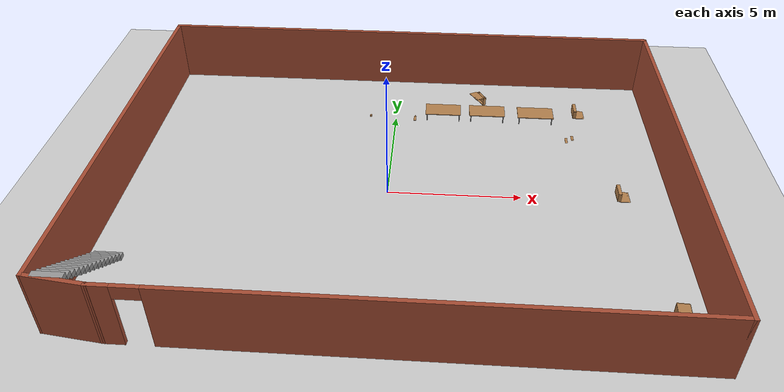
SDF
<sdf version="1.7">
 <world name="default">
  <plugin name="gazebo_link_attacher" filename="libgazebo_link_attacher.so"/>
  <light name="sun" type="directional">
   <pose>0 0 10 0 -0 0</pose>
   <diffuse>0.8 0.8 0.8 1</diffuse>
   <specular>0.2 0.2 0.2 1</specular>
   <attenuation>
    <range>1000</range>
    <constant>0.9</constant>
    <linear>0.01</linear>
    <quadratic>0.001</quadratic>
   </attenuation>
   <direction>-0.5 0.1 -0.9</direction>
   <spot><inner_angle>0</inner_angle><outer_angle>0</outer_angle><falloff>0</falloff></spot>
  </light>
  <model name="ground_plane">
   <static>1</static>
   <link name="link">
    <collision name="collision">
     <geometry><plane><normal>0 0 1</normal><size>100 100</size></plane></geometry>
     <surface><friction><ode><mu>100</mu><mu2>50</mu2></ode></friction></surface>
    </collision>
    <visual name="visual">
     <cast_shadows>0</cast_shadows>
     <geometry><plane><normal>0 0 1</normal><size>100 100</size></plane></geometry>
     <material>
      <script><uri>file://media/materials/scripts/gazebo.material</uri><name>Gazebo/Grey</name></script>
     </material>
    </visual>
   </link>
  </model>
  <gravity>0 0 -9.8</gravity>
  <magnetic_field>6e-06 2.3e-05 -4.2e-05</magnetic_field>
  <atmosphere type="adiabatic"/>
  <physics type="ode">
   <max_step_size>0.001</max_step_size>
   <real_time_factor>1</real_time_factor>
   <real_time_update_rate>1000</real_time_update_rate>
  </physics>
  <scene><ambient>0.4 0.4 0.4 1</ambient><background>0.7 0.7 0.7 1</background><shadows>1</shadows></scene>
  <audio><device>default</device></audio>
  <spherical_coordinates>
   <surface_model>EARTH_WGS84</surface_model>
   <latitude_deg>0</latitude_deg>
   <longitude_deg>0</longitude_deg>
   <elevation>0</elevation>
   <heading_deg>0</heading_deg>
  </spherical_coordinates>
  <model name="Untitled">
   <pose>0.302416 0.205559 0 0 -0 0</pose>
   <link name="Stairs_0">
    <visual name="Stairs_0_Visual_0">
     <pose>-9.52086 -4.35961 0.083333 0 -0 0</pose>
     <geometry><box><size>1 0.233333 0.166667</size></box></geometry>
     <material>
      <script><uri>file://media/materials/scripts/gazebo.material</uri><name>Gazebo/Grey</name></script>
      <ambient>1 1 1 1</ambient>
     </material>
     <meta><layer>0</layer></meta>
    </visual>
    <collision name="Stairs_0_Collision_0">
     <geometry><box><size>1 0.233333 0.166667</size></box></geometry>
     <pose>-9.52086 -4.35961 0.083333 0 -0 0</pose>
    </collision>
    <visual name="Stairs_0_Visual_1">
     <pose>-9.52086 -4.59294 0.25 0 -0 0</pose>
     <geometry><box><size>1 0.233333 0.166667</size></box></geometry>
     <material>
      <script><uri>file://media/materials/scripts/gazebo.material</uri><name>Gazebo/Grey</name></script>
      <ambient>1 1 1 1</ambient>
     </material>
     <meta><layer>0</layer></meta>
    </visual>
    <collision name="Stairs_0_Collision_1">
     <geometry><box><size>1 0.233333 0.166667</size></box></geometry>
     <pose>-9.52086 -4.59294 0.25 0 -0 0</pose>
    </collision>
    <visual name="Stairs_0_Visual_2">
     <pose>-9.52086 -4.82628 0.416667 0 -0 0</pose>
     <geometry><box><size>1 0.233333 0.166667</size></box></geometry>
     <material>
      <script><uri>file://media/materials/scripts/gazebo.material</uri><name>Gazebo/Grey</name></script>
      <ambient>1 1 1 1</ambient>
     </material>
     <meta><layer>0</layer></meta>
    </visual>
    <collision name="Stairs_0_Collision_2">
     <geometry><box><size>1 0.233333 0.166667</size></box></geometry>
     <pose>-9.52086 -4.82628 0.416667 0 -0 0</pose>
    </collision>
    <visual name="Stairs_0_Visual_3">
     <pose>-9.52086 -5.05961 0.583333 0 -0 0</pose>
     <geometry><box><size>1 0.233333 0.166667</size></box></geometry>
     <material>
      <script><uri>file://media/materials/scripts/gazebo.material</uri><name>Gazebo/Grey</name></script>
      <ambient>1 1 1 1</ambient>
     </material>
     <meta><layer>0</layer></meta>
    </visual>
    <collision name="Stairs_0_Collision_3">
     <geometry><box><size>1 0.233333 0.166667</size></box></geometry>
     <pose>-9.52086 -5.05961 0.583333 0 -0 0</pose>
    </collision>
    <visual name="Stairs_0_Visual_4">
     <pose>-9.52086 -5.29294 0.75 0 -0 0</pose>
     <geometry><box><size>1 0.233333 0.166667</size></box></geometry>
     <material>
      <script><uri>file://media/materials/scripts/gazebo.material</uri><name>Gazebo/Grey</name></script>
      <ambient>1 1 1 1</ambient>
     </material>
     <meta><layer>0</layer></meta>
    </visual>
    <collision name="Stairs_0_Collision_4">
     <geometry><box><size>1 0.233333 0.166667</size></box></geometry>
     <pose>-9.52086 -5.29294 0.75 0 -0 0</pose>
    </collision>
    <visual name="Stairs_0_Visual_5">
     <pose>-9.52086 -5.52628 0.916667 0 -0 0</pose>
     <geometry><box><size>1 0.233333 0.166667</size></box></geometry>
     <material>
      <script><uri>file://media/materials/scripts/gazebo.material</uri><name>Gazebo/Grey</name></script>
      <ambient>1 1 1 1</ambient>
     </material>
     <meta><layer>0</layer></meta>
    </visual>
    <collision name="Stairs_0_Collision_5">
     <geometry><box><size>1 0.233333 0.166667</size></box></geometry>
     <pose>-9.52086 -5.52628 0.916667 0 -0 0</pose>
    </collision>
    <visual name="Stairs_0_Visual_6">
     <pose>-9.52086 -5.75961 1.08333 0 -0 0</pose>
     <geometry><box><size>1 0.233333 0.166667</size></box></geometry>
     <material>
      <script><uri>file://media/materials/scripts/gazebo.material</uri><name>Gazebo/Grey</name></script>
      <ambient>1 1 1 1</ambient>
     </material>
     <meta><layer>0</layer></meta>
    </visual>
    <collision name="Stairs_0_Collision_6">
     <geometry><box><size>1 0.233333 0.166667</size></box></geometry>
     <pose>-9.52086 -5.75961 1.08333 0 -0 0</pose>
    </collision>
    <visual name="Stairs_0_Visual_7">
     <pose>-9.52086 -5.99294 1.25 0 -0 0</pose>
     <geometry><box><size>1 0.233333 0.166667</size></box></geometry>
     <material>
      <script><uri>file://media/materials/scripts/gazebo.material</uri><name>Gazebo/Grey</name></script>
      <ambient>1 1 1 1</ambient>
     </material>
     <meta><layer>0</layer></meta>
    </visual>
    <collision name="Stairs_0_Collision_7">
     <geometry><box><size>1 0.233333 0.166667</size></box></geometry>
     <pose>-9.52086 -5.99294 1.25 0 -0 0</pose>
    </collision>
    <visual name="Stairs_0_Visual_8">
     <pose>-9.52086 -6.22628 1.41667 0 -0 0</pose>
     <geometry><box><size>1 0.233333 0.166667</size></box></geometry>
     <material>
      <script><uri>file://media/materials/scripts/gazebo.material</uri><name>Gazebo/Grey</name></script>
      <ambient>1 1 1 1</ambient>
     </material>
     <meta><layer>0</layer></meta>
    </visual>
    <collision name="Stairs_0_Collision_8">
     <geometry><box><size>1 0.233333 0.166667</size></box></geometry>
     <pose>-9.52086 -6.22628 1.41667 0 -0 0</pose>
    </collision>
    <visual name="Stairs_0_Visual_9">
     <pose>-9.52086 -6.45961 1.58333 0 -0 0</pose>
     <geometry><box><size>1 0.233333 0.166667</size></box></geometry>
     <material>
      <script><uri>file://media/materials/scripts/gazebo.material</uri><name>Gazebo/Grey</name></script>
      <ambient>1 1 1 1</ambient>
     </material>
     <meta><layer>0</layer></meta>
    </visual>
    <collision name="Stairs_0_Collision_9">
     <geometry><box><size>1 0.233333 0.166667</size></box></geometry>
     <pose>-9.52086 -6.45961 1.58333 0 -0 0</pose>
    </collision>
    <visual name="Stairs_0_Visual_10">
     <pose>-9.52086 -6.69294 1.75 0 -0 0</pose>
     <geometry><box><size>1 0.233333 0.166667</size></box></geometry>
     <material>
      <script><uri>file://media/materials/scripts/gazebo.material</uri><name>Gazebo/Grey</name></script>
      <ambient>1 1 1 1</ambient>
     </material>
     <meta><layer>0</layer></meta>
    </visual>
    <collision name="Stairs_0_Collision_10">
     <geometry><box><size>1 0.233333 0.166667</size></box></geometry>
     <pose>-9.52086 -6.69294 1.75 0 -0 0</pose>
    </collision>
    <visual name="Stairs_0_Visual_11">
     <pose>-9.52086 -6.92628 1.91667 0 -0 0</pose>
     <geometry><box><size>1 0.233333 0.166667</size></box></geometry>
     <material>
      <script><uri>file://media/materials/scripts/gazebo.material</uri><name>Gazebo/Grey</name></script>
      <ambient>1 1 1 1</ambient>
     </material>
     <meta><layer>0</layer></meta>
    </visual>
    <collision name="Stairs_0_Collision_11">
     <geometry><box><size>1 0.233333 0.166667</size></box></geometry>
     <pose>-9.52086 -6.92628 1.91667 0 -0 0</pose>
    </collision>
    <visual name="Stairs_0_Visual_12">
     <pose>-9.52086 -7.15961 2.08333 0 -0 0</pose>
     <geometry><box><size>1 0.233333 0.166667</size></box></geometry>
     <material>
      <script><uri>file://media/materials/scripts/gazebo.material</uri><name>Gazebo/Grey</name></script>
      <ambient>1 1 1 1</ambient>
     </material>
     <meta><layer>0</layer></meta>
    </visual>
    <collision name="Stairs_0_Collision_12">
     <geometry><box><size>1 0.233333 0.166667</size></box></geometry>
     <pose>-9.52086 -7.15961 2.08333 0 -0 0</pose>
    </collision>
    <visual name="Stairs_0_Visual_13">
     <pose>-9.52086 -7.39294 2.25 0 -0 0</pose>
     <geometry><box><size>1 0.233333 0.166667</size></box></geometry>
     <material>
      <script><uri>file://media/materials/scripts/gazebo.material</uri><name>Gazebo/Grey</name></script>
      <ambient>1 1 1 1</ambient>
     </material>
     <meta><layer>0</layer></meta>
    </visual>
    <collision name="Stairs_0_Collision_13">
     <geometry><box><size>1 0.233333 0.166667</size></box></geometry>
     <pose>-9.52086 -7.39294 2.25 0 -0 0</pose>
    </collision>
    <visual name="Stairs_0_Visual_14">
     <pose>-9.52086 -7.62628 2.41667 0 -0 0</pose>
     <geometry><box><size>1 0.233333 0.166667</size></box></geometry>
     <material>
      <script><uri>file://media/materials/scripts/gazebo.material</uri><name>Gazebo/Grey</name></script>
      <ambient>1 1 1 1</ambient>
     </material>
     <meta><layer>0</layer></meta>
    </visual>
    <collision name="Stairs_0_Collision_14">
     <geometry><box><size>1 0.233333 0.166667</size></box></geometry>
     <pose>-9.52086 -7.62628 2.41667 0 -0 0</pose>
    </collision>
   </link>
   <link name="Wall_1">
    <pose>1.00436 -7.92064 0 0 -0 0</pose>
    <visual name="Wall_1_Visual_0">
     <pose>-8.99137 0 1.25 0 -0 0</pose>
     <geometry><box><size>0.767258 0.15 2.5</size></box></geometry>
     <material>
      <script><uri>file://media/materials/scripts/gazebo.material</uri><name>Gazebo/Bricks</name></script>
      <ambient>1 1 1 1</ambient>
     </material>
     <meta><layer>0</layer></meta>
    </visual>
    <collision name="Wall_1_Collision_0">
     <geometry><box><size>0.767258 0.15 2.5</size></box></geometry>
     <pose>-8.99137 0 1.25 0 -0 0</pose>
    </collision>
    <visual name="Wall_1_Visual_1">
     <pose>0.833629 0 1.25 0 -0 0</pose>
     <geometry><box><size>17.0827 0.15 2.5</size></box></geometry>
     <material>
      <script><uri>file://media/materials/scripts/gazebo.material</uri><name>Gazebo/Bricks</name></script>
      <ambient>1 1 1 1</ambient>
     </material>
     <meta><layer>0</layer></meta>
    </visual>
    <collision name="Wall_1_Collision_1">
     <geometry><box><size>17.0827 0.15 2.5</size></box></geometry>
     <pose>0.833629 0 1.25 0 -0 0</pose>
    </collision>
    <visual name="Wall_1_Visual_2">
     <pose>-8.15774 0 2.25 0 -0 0</pose>
     <geometry><box><size>0.9 0.15 0.5</size></box></geometry>
     <material>
      <script><uri>file://media/materials/scripts/gazebo.material</uri><name>Gazebo/Bricks</name></script>
      <ambient>1 1 1 1</ambient>
     </material>
     <meta><layer>0</layer></meta>
    </visual>
    <collision name="Wall_1_Collision_2">
     <geometry><box><size>0.9 0.15 0.5</size></box></geometry>
     <pose>-8.15774 0 2.25 0 -0 0</pose>
    </collision>
   </link>
   <link name="Wall_2">
    <collision name="Wall_2_Collision">
     <geometry><box><size>16 0.15 2.5</size></box></geometry>
     <pose>0 0 1.25 0 -0 0</pose>
    </collision>
    <visual name="Wall_2_Visual">
     <pose>0 0 1.25 0 -0 0</pose>
     <geometry><box><size>16 0.15 2.5</size></box></geometry>
     <material>
      <script><uri>file://media/materials/scripts/gazebo.material</uri><name>Gazebo/Bricks</name></script>
      <ambient>1 1 1 1</ambient>
     </material>
     <meta><layer>0</layer></meta>
    </visual>
    <pose>10.3044 0.004361 0 0 -0 1.5708</pose>
   </link>
   <link name="Wall_3">
    <collision name="Wall_3_Collision">
     <geometry><box><size>20.75 0.15 2.5</size></box></geometry>
     <pose>0 0 1.25 0 -0 0</pose>
    </collision>
    <visual name="Wall_3_Visual">
     <pose>0 0 1.25 0 -0 0</pose>
     <geometry><box><size>20.75 0.15 2.5</size></box></geometry>
     <material>
      <script><uri>file://media/materials/scripts/gazebo.material</uri><name>Gazebo/Bricks</name></script>
      <ambient>1 1 1 1</ambient>
     </material>
     <meta><layer>0</layer></meta>
    </visual>
    <pose>0.004362 7.92936 0 0 -0 3.14159</pose>
   </link>
   <link name="Wall_4">
    <collision name="Wall_4_Collision">
     <geometry><box><size>15.75 0.15 2.5</size></box></geometry>
     <pose>0 0 1.25 0 -0 0</pose>
    </collision>
    <visual name="Wall_4_Visual">
     <pose>0 0 1.25 0 -0 0</pose>
     <geometry><box><size>15.75 0.15 2.5</size></box></geometry>
     <material>
      <script><uri>file://media/materials/scripts/gazebo.material</uri><name>Gazebo/Bricks</name></script>
      <ambient>1 1 1 1</ambient>
     </material>
     <meta><layer>0</layer></meta>
    </visual>
    <pose>-10.2956 0.129361 0 0 -0 -1.5708</pose>
   </link>
   <link name="Wall_5">
    <collision name="Wall_5_Collision">
     <geometry><box><size>2.16556 0.15 2.5</size></box></geometry>
     <pose>0 0 1.25 0 -0 0</pose>
    </collision>
    <visual name="Wall_5_Visual">
     <pose>0 0 1.25 0 -0 0</pose>
     <geometry><box><size>2.16556 0.15 2.5</size></box></geometry>
     <material>
      <script><uri>file://media/materials/scripts/gazebo.material</uri><name>Gazebo/Bricks</name></script>
      <ambient>1 1 1 1</ambient>
     </material>
     <meta><layer>0</layer></meta>
    </visual>
    <pose>-9.29564 -7.79564 0 0 -0 -0.124355</pose>
   </link>
   <static>1</static>
  </model>
  <model name="table">
   <static>1</static>
   <link name="link">
    <collision name="surface">
     <pose>0 0 1 0 -0 0</pose>
     <geometry><box><size>1.5 0.8 0.03</size></box></geometry>
     <surface><friction><ode><mu>0.6</mu><mu2>0.6</mu2></ode></friction></surface>
    </collision>
    <visual name="visual1">
     <pose>0 0 1 0 -0 0</pose>
     <geometry><box><size>1.5 0.8 0.03</size></box></geometry>
     <material>
      <script><uri>file://media/materials/scripts/gazebo.material</uri><name>Gazebo/Wood</name></script>
     </material>
    </visual>
    <collision name="front_left_leg">
     <pose>0.68 0.38 0.5 0 -0 0</pose>
     <geometry><cylinder><radius>0.02</radius><length>1</length></cylinder></geometry>
    </collision>
    <visual name="front_left_leg">
     <pose>0.68 0.38 0.5 0 -0 0</pose>
     <geometry><cylinder><radius>0.02</radius><length>1</length></cylinder></geometry>
     <material>
      <script><uri>file://media/materials/scripts/gazebo.material</uri><name>Gazebo/Grey</name></script>
     </material>
    </visual>
    <collision name="front_right_leg">
     <pose>0.68 -0.38 0.5 0 -0 0</pose>
     <geometry><cylinder><radius>0.02</radius><length>1</length></cylinder></geometry>
    </collision>
    <visual name="front_right_leg">
     <pose>0.68 -0.38 0.5 0 -0 0</pose>
     <geometry><cylinder><radius>0.02</radius><length>1</length></cylinder></geometry>
     <material>
      <script><uri>file://media/materials/scripts/gazebo.material</uri><name>Gazebo/Grey</name></script>
     </material>
    </visual>
    <collision name="back_right_leg">
     <pose>-0.68 -0.38 0.5 0 -0 0</pose>
     <geometry><cylinder><radius>0.02</radius><length>1</length></cylinder></geometry>
    </collision>
    <visual name="back_right_leg">
     <pose>-0.68 -0.38 0.5 0 -0 0</pose>
     <geometry><cylinder><radius>0.02</radius><length>1</length></cylinder></geometry>
     <material>
      <script><uri>file://media/materials/scripts/gazebo.material</uri><name>Gazebo/Grey</name></script>
     </material>
    </visual>
    <collision name="back_left_leg">
     <pose>-0.68 0.38 0.5 0 -0 0</pose>
     <geometry><cylinder><radius>0.02</radius><length>1</length></cylinder></geometry>
    </collision>
    <visual name="back_left_leg">
     <pose>-0.68 0.38 0.5 0 -0 0</pose>
     <geometry><cylinder><radius>0.02</radius><length>1</length></cylinder></geometry>
     <material>
      <script><uri>file://media/materials/scripts/gazebo.material</uri><name>Gazebo/Grey</name></script>
     </material>
    </visual>
   </link>
   <pose>5.91005 5.39504 -0.713216 0 -0 0</pose>
  </model>
  <model name="wooden_board">
   <link name="base">
    <pose>0 0 0.00523 0 -0 0</pose>
    <inertial>
     <mass>0.2765</mass>
     <inertia>
      <ixx>0.0025148</ixx>
      <ixy>0</ixy>
      <ixz>0</ixz>
      <iyy>0.00024037</iyy>
      <iyz>0</iyz>
      <izz>0.00275013</izz>
     </inertia>
    </inertial>
    <collision name="collision">
     <geometry><box><size>0.1016 0.3302 0.01046</size></box></geometry>
     <surface>
      <contact>
       <poissons_ratio>0.347</poissons_ratio>
       <elastic_modulus>8.8e+09</elastic_modulus>
       <ode><kp>100000</kp><kd>100</kd><max_vel>100</max_vel><min_depth>0.001</min_depth></ode>
      </contact>
      <friction>
       <torsional>
        <coefficient>1</coefficient>
        <use_patch_radius>0</use_patch_radius>
        <surface_radius>0.01</surface_radius>
       </torsional>
      </friction>
     </surface>
    </collision>
    <visual name="visual">
     <geometry><box><size>0.1016 0.3302 0.01046</size></box></geometry>
     <material>
      <script><uri>file://media/materials/scripts/gazebo.material</uri><name>Gazebo/Wood</name></script>
     </material>
    </visual>
    <visual name="tee_nut_1">
     <pose>0 -0.116 0 0 -0 0</pose>
     <geometry><cylinder><radius>0.00635</radius><length>0.0105646</length></cylinder></geometry>
     <material>
      <script><uri>file://media/materials/scripts/gazebo.material</uri><name>Gazebo/Grey</name></script>
     </material>
    </visual>
    <visual name="tee_nut_2">
     <pose>0 -0.038 0 0 -0 0</pose>
     <geometry><cylinder><radius>0.00635</radius><length>0.0105646</length></cylinder></geometry>
     <material>
      <script><uri>file://media/materials/scripts/gazebo.material</uri><name>Gazebo/Grey</name></script>
     </material>
    </visual>
    <visual name="tee_nut_3">
     <pose>0 0.038 0 0 -0 0</pose>
     <geometry><cylinder><radius>0.00635</radius><length>0.0105646</length></cylinder></geometry>
     <material>
      <script><uri>file://media/materials/scripts/gazebo.material</uri><name>Gazebo/Grey</name></script>
     </material>
    </visual>
    <visual name="tee_nut_4">
     <pose>0 0.116 0 0 -0 0</pose>
     <geometry><cylinder><radius>0.00635</radius><length>0.0105646</length></cylinder></geometry>
     <material>
      <script><uri>file://media/materials/scripts/gazebo.material</uri><name>Gazebo/Grey</name></script>
     </material>
    </visual>
   </link>
   <pose>7.09779 3.84602 -0.001007 0 -0 0</pose>
  </model>
  <model name="bookshelf">
   <static>1</static>
   <link name="link">
    <inertial><mass>1</mass></inertial>
    <collision name="back">
     <pose>0 0.005 0.6 0 -0 0</pose>
     <geometry><box><size>0.9 0.01 1.2</size></box></geometry>
    </collision>
    <visual name="visual1">
     <pose>0 0.005 0.6 0 -0 0</pose>
     <geometry><box><size>0.9 0.01 1.2</size></box></geometry>
     <material>
      <script><uri>file://media/materials/scripts/gazebo.material</uri><name>Gazebo/Wood</name></script>
     </material>
    </visual>
    <collision name="left_side">
     <pose>0.45 -0.195 0.6 0 -0 0</pose>
     <geometry><box><size>0.02 0.4 1.2</size></box></geometry>
    </collision>
    <visual name="visual2">
     <pose>0.45 -0.195 0.6 0 -0 0</pose>
     <geometry><box><size>0.02 0.4 1.2</size></box></geometry>
     <material>
      <script><uri>file://media/materials/scripts/gazebo.material</uri><name>Gazebo/Wood</name></script>
     </material>
    </visual>
    <collision name="right_side">
     <pose>-0.45 -0.195 0.6 0 -0 0</pose>
     <geometry><box><size>0.02 0.4 1.2</size></box></geometry>
    </collision>
    <visual name="visual3">
     <pose>-0.45 -0.195 0.6 0 -0 0</pose>
     <geometry><box><size>0.02 0.4 1.2</size></box></geometry>
     <material>
      <script><uri>file://media/materials/scripts/gazebo.material</uri><name>Gazebo/Wood</name></script>
     </material>
    </visual>
    <collision name="bottom">
     <pose>0 -0.195 0.03 0 -0 0</pose>
     <geometry><box><size>0.88 0.4 0.06</size></box></geometry>
    </collision>
    <visual name="visual4">
     <pose>0 -0.195 0.03 0 -0 0</pose>
     <geometry><box><size>0.88 0.4 0.06</size></box></geometry>
     <material>
      <script><uri>file://media/materials/scripts/gazebo.material</uri><name>Gazebo/Wood</name></script>
     </material>
    </visual>
    <collision name="top">
     <pose>0 -0.195 1.19 0 -0 0</pose>
     <geometry><box><size>0.88 0.4 0.02</size></box></geometry>
    </collision>
    <visual name="visual5">
     <pose>0 -0.195 1.19 0 -0 0</pose>
     <geometry><box><size>0.88 0.4 0.02</size></box></geometry>
     <material>
      <script><uri>file://media/materials/scripts/gazebo.material</uri><name>Gazebo/Wood</name></script>
     </material>
    </visual>
    <collision name="low_shelf">
     <pose>0 -0.195 0.43 0 -0 0</pose>
     <geometry><box><size>0.88 0.4 0.02</size></box></geometry>
    </collision>
    <visual name="visual6">
     <pose>0 -0.195 0.43 0 -0 0</pose>
     <geometry><box><size>0.88 0.4 0.02</size></box></geometry>
     <material>
      <script><uri>file://media/materials/scripts/gazebo.material</uri><name>Gazebo/Wood</name></script>
     </material>
    </visual>
    <collision name="high_shelf">
     <pose>0 -0.195 0.8 0 -0 0</pose>
     <geometry><box><size>0.88 0.4 0.02</size></box></geometry>
    </collision>
    <visual name="visual7">
     <pose>0 -0.195 0.8 0 -0 0</pose>
     <geometry><box><size>0.88 0.4 0.02</size></box></geometry>
     <material>
      <script><uri>file://media/materials/scripts/gazebo.material</uri><name>Gazebo/Wood</name></script>
     </material>
    </visual>
   </link>
   <pose>9.5222 -6.52823 -0.009255 0.019523 0.001491 -1.64703</pose>
  </model>
  <model name="table_clone">
   <static>1</static>
   <link name="link">
    <collision name="surface">
     <pose>0 0 1 0 -0 0</pose>
     <geometry><box><size>1.5 0.8 0.03</size></box></geometry>
     <surface><friction><ode><mu>0.6</mu><mu2>0.6</mu2></ode></friction></surface>
    </collision>
    <visual name="visual1">
     <pose>0 0 1 0 -0 0</pose>
     <geometry><box><size>1.5 0.8 0.03</size></box></geometry>
     <material>
      <script><uri>file://media/materials/scripts/gazebo.material</uri><name>Gazebo/Wood</name></script>
     </material>
    </visual>
    <collision name="front_left_leg">
     <pose>0.68 0.38 0.5 0 -0 0</pose>
     <geometry><cylinder><radius>0.02</radius><length>1</length></cylinder></geometry>
    </collision>
    <visual name="front_left_leg">
     <pose>0.68 0.38 0.5 0 -0 0</pose>
     <geometry><cylinder><radius>0.02</radius><length>1</length></cylinder></geometry>
     <material>
      <script><uri>file://media/materials/scripts/gazebo.material</uri><name>Gazebo/Grey</name></script>
     </material>
    </visual>
    <collision name="front_right_leg">
     <pose>0.68 -0.38 0.5 0 -0 0</pose>
     <geometry><cylinder><radius>0.02</radius><length>1</length></cylinder></geometry>
    </collision>
    <visual name="front_right_leg">
     <pose>0.68 -0.38 0.5 0 -0 0</pose>
     <geometry><cylinder><radius>0.02</radius><length>1</length></cylinder></geometry>
     <material>
      <script><uri>file://media/materials/scripts/gazebo.material</uri><name>Gazebo/Grey</name></script>
     </material>
    </visual>
    <collision name="back_right_leg">
     <pose>-0.68 -0.38 0.5 0 -0 0</pose>
     <geometry><cylinder><radius>0.02</radius><length>1</length></cylinder></geometry>
    </collision>
    <visual name="back_right_leg">
     <pose>-0.68 -0.38 0.5 0 -0 0</pose>
     <geometry><cylinder><radius>0.02</radius><length>1</length></cylinder></geometry>
     <material>
      <script><uri>file://media/materials/scripts/gazebo.material</uri><name>Gazebo/Grey</name></script>
     </material>
    </visual>
    <collision name="back_left_leg">
     <pose>-0.68 0.38 0.5 0 -0 0</pose>
     <geometry><cylinder><radius>0.02</radius><length>1</length></cylinder></geometry>
    </collision>
    <visual name="back_left_leg">
     <pose>-0.68 0.38 0.5 0 -0 0</pose>
     <geometry><cylinder><radius>0.02</radius><length>1</length></cylinder></geometry>
     <material>
      <script><uri>file://media/materials/scripts/gazebo.material</uri><name>Gazebo/Grey</name></script>
     </material>
    </visual>
   </link>
   <pose>3.86348 5.41388 -0.713216 0 -0 0</pose>
  </model>
  <model name="table_clone_0">
   <static>1</static>
   <link name="link">
    <collision name="surface">
     <pose>0 0 1 0 -0 0</pose>
     <geometry><box><size>1.5 0.8 0.03</size></box></geometry>
     <surface><friction><ode><mu>0.6</mu><mu2>0.6</mu2></ode></friction></surface>
    </collision>
    <visual name="visual1">
     <pose>0 0 1 0 -0 0</pose>
     <geometry><box><size>1.5 0.8 0.03</size></box></geometry>
     <material>
      <script><uri>file://media/materials/scripts/gazebo.material</uri><name>Gazebo/Wood</name></script>
     </material>
    </visual>
    <collision name="front_left_leg">
     <pose>0.68 0.38 0.5 0 -0 0</pose>
     <geometry><cylinder><radius>0.02</radius><length>1</length></cylinder></geometry>
    </collision>
    <visual name="front_left_leg">
     <pose>0.68 0.38 0.5 0 -0 0</pose>
     <geometry><cylinder><radius>0.02</radius><length>1</length></cylinder></geometry>
     <material>
      <script><uri>file://media/materials/scripts/gazebo.material</uri><name>Gazebo/Grey</name></script>
     </material>
    </visual>
    <collision name="front_right_leg">
     <pose>0.68 -0.38 0.5 0 -0 0</pose>
     <geometry><cylinder><radius>0.02</radius><length>1</length></cylinder></geometry>
    </collision>
    <visual name="front_right_leg">
     <pose>0.68 -0.38 0.5 0 -0 0</pose>
     <geometry><cylinder><radius>0.02</radius><length>1</length></cylinder></geometry>
     <material>
      <script><uri>file://media/materials/scripts/gazebo.material</uri><name>Gazebo/Grey</name></script>
     </material>
    </visual>
    <collision name="back_right_leg">
     <pose>-0.68 -0.38 0.5 0 -0 0</pose>
     <geometry><cylinder><radius>0.02</radius><length>1</length></cylinder></geometry>
    </collision>
    <visual name="back_right_leg">
     <pose>-0.68 -0.38 0.5 0 -0 0</pose>
     <geometry><cylinder><radius>0.02</radius><length>1</length></cylinder></geometry>
     <material>
      <script><uri>file://media/materials/scripts/gazebo.material</uri><name>Gazebo/Grey</name></script>
     </material>
    </visual>
    <collision name="back_left_leg">
     <pose>-0.68 0.38 0.5 0 -0 0</pose>
     <geometry><cylinder><radius>0.02</radius><length>1</length></cylinder></geometry>
    </collision>
    <visual name="back_left_leg">
     <pose>-0.68 0.38 0.5 0 -0 0</pose>
     <geometry><cylinder><radius>0.02</radius><length>1</length></cylinder></geometry>
     <material>
      <script><uri>file://media/materials/scripts/gazebo.material</uri><name>Gazebo/Grey</name></script>
     </material>
    </visual>
   </link>
   <pose>1.99959 5.40368 -0.713216 0 -0 0</pose>
  </model>
  <model name="wooden_peg_board">
   <frame name="wooden_board::__model__" attached_to="wooden_board::base">
    <pose relative_to="__model__">0 0 0 0 -0 0</pose>
   </frame>
   <link name="wooden_board::base">
    <pose relative_to="wooden_board::__model__">0 0 0.00523 0 -0 0</pose>
    <inertial>
     <mass>0.2765</mass>
     <inertia>
      <ixx>0.0025148</ixx>
      <ixy>0</ixy>
      <ixz>0</ixz>
      <iyy>0.00024037</iyy>
      <iyz>0</iyz>
      <izz>0.00275013</izz>
     </inertia>
    </inertial>
    <collision name="collision">
     <geometry><box><size>0.1016 0.3302 0.01046</size></box></geometry>
     <surface>
      <contact>
       <poissons_ratio>0.347</poissons_ratio>
       <elastic_modulus>8.8e+09</elastic_modulus>
       <ode><kp>100000</kp><kd>100</kd><max_vel>100</max_vel><min_depth>0.001</min_depth></ode>
      </contact>
      <friction>
       <torsional>
        <coefficient>1</coefficient>
        <use_patch_radius>0</use_patch_radius>
        <surface_radius>0.01</surface_radius>
       </torsional>
      </friction>
     </surface>
    </collision>
    <visual name="visual">
     <geometry><box><size>0.1016 0.3302 0.01046</size></box></geometry>
     <material>
      <script><uri>file://media/materials/scripts/gazebo.material</uri><name>Gazebo/Wood</name></script>
     </material>
    </visual>
    <visual name="tee_nut_1">
     <pose>0 -0.116 0 0 -0 0</pose>
     <geometry><cylinder><radius>0.00635</radius><length>0.0105646</length></cylinder></geometry>
     <material>
      <script><uri>file://media/materials/scripts/gazebo.material</uri><name>Gazebo/Grey</name></script>
     </material>
    </visual>
    <visual name="tee_nut_2">
     <pose>0 -0.038 0 0 -0 0</pose>
     <geometry><cylinder><radius>0.00635</radius><length>0.0105646</length></cylinder></geometry>
     <material>
      <script><uri>file://media/materials/scripts/gazebo.material</uri><name>Gazebo/Grey</name></script>
     </material>
    </visual>
    <visual name="tee_nut_3">
     <pose>0 0.038 0 0 -0 0</pose>
     <geometry><cylinder><radius>0.00635</radius><length>0.0105646</length></cylinder></geometry>
     <material>
      <script><uri>file://media/materials/scripts/gazebo.material</uri><name>Gazebo/Grey</name></script>
     </material>
    </visual>
    <visual name="tee_nut_4">
     <pose>0 0.116 0 0 -0 0</pose>
     <geometry><cylinder><radius>0.00635</radius><length>0.0105646</length></cylinder></geometry>
     <material>
      <script><uri>file://media/materials/scripts/gazebo.material</uri><name>Gazebo/Grey</name></script>
     </material>
    </visual>
   </link>
   <frame name="peg::__model__" attached_to="peg::link">
    <pose relative_to="__model__">0 0.116 0 0 -0 0</pose>
   </frame>
   <link name="peg::link">
    <pose relative_to="peg::__model__">0 0 0.04 0 -0 0</pose>
    <inertial>
     <mass>0.0175</mass>
     <inertia>
      <ixx>9.74923e-06</ixx>
      <ixy>0</ixy>
      <ixz>0</ixz>
      <iyy>9.74923e-06</iyy>
      <iyz>0</iyz>
      <izz>8.31797e-07</izz>
     </inertia>
    </inertial>
    <collision name="collision">
     <geometry><cylinder><radius>0.00975</radius><length>0.08</length></cylinder></geometry>
     <surface>
      <contact>
       <poissons_ratio>0.347</poissons_ratio>
       <elastic_modulus>8.8e+09</elastic_modulus>
       <ode><kp>100000</kp><kd>100</kd><max_vel>100</max_vel><min_depth>0.001</min_depth></ode>
      </contact>
      <friction>
       <torsional>
        <coefficient>1</coefficient>
        <use_patch_radius>0</use_patch_radius>
        <surface_radius>0.01</surface_radius>
       </torsional>
      </friction>
     </surface>
    </collision>
    <visual name="visual">
     <geometry><cylinder><radius>0.00975</radius><length>0.08</length></cylinder></geometry>
     <material>
      <script><uri>file://media/materials/scripts/gazebo.material</uri><name>Gazebo/Wood</name></script>
     </material>
    </visual>
   </link>
   <joint name="board_peg" type="revolute">
    <parent>wooden_board::base</parent>
    <child>peg::link</child>
    <axis>
     <xyz>0 0 1</xyz>
     <limit><upper>0</upper><lower>0</lower></limit>
     <dynamics><spring_reference>0</spring_reference><spring_stiffness>0</spring_stiffness></dynamics>
    </axis>
   </joint>
   <pose>0.79943 5.08483 -0.001004 1.3e-05 -1e-06 -1e-06</pose>
  </model>
  <model name="wooden_case_metal_peg">
   <frame name="wooden_case::__model__" attached_to="wooden_case::base">
    <pose relative_to="__model__">0 0 0 0 -0 0</pose>
   </frame>
   <link name="wooden_case::base">
    <pose relative_to="wooden_case::__model__">0 0 0.024 0 -0 0</pose>
    <inertial>
     <pose>-0.022184 0 0.171592 0 -0 0</pose>
     <mass>3.96264</mass>
     <inertia>
      <ixx>0.213536</ixx>
      <ixy>0</ixy>
      <ixz>0.000779377</ixz>
      <iyy>0.0708943</iyy>
      <iyz>0</iyz>
      <izz>0.154604</izz>
     </inertia>
    </inertial>
    <collision name="collision_back">
     <pose>-0.053975 0 0.1778 0 -0 0</pose>
     <geometry><box><size>0.01905 0.5461 0.3175</size></box></geometry>
     <surface>
      <contact>
       <poissons_ratio>0.347</poissons_ratio>
       <elastic_modulus>8.8e+09</elastic_modulus>
       <ode><kp>100000</kp><kd>100</kd><max_vel>100</max_vel><min_depth>0.001</min_depth></ode>
      </contact>
      <friction>
       <torsional>
        <coefficient>1</coefficient>
        <use_patch_radius>0</use_patch_radius>
        <surface_radius>0.01</surface_radius>
       </torsional>
      </friction>
     </surface>
    </collision>
    <visual name="visual_back">
     <pose>-0.053975 0 0.1778 0 -0 0</pose>
     <geometry><box><size>0.01905 0.5461 0.3175</size></box></geometry>
     <material>
      <script><uri>file://media/materials/scripts/gazebo.material</uri><name>Gazebo/Wood</name></script>
     </material>
    </visual>
    <collision name="collision_bottom">
     <pose>0 0 0.009525 0 -0 0</pose>
     <geometry><box><size>0.127 0.5842 0.01905</size></box></geometry>
     <surface>
      <contact>
       <poissons_ratio>0.347</poissons_ratio>
       <elastic_modulus>8.8e+09</elastic_modulus>
       <ode><kp>100000</kp><kd>100</kd><max_vel>100</max_vel><min_depth>0.001</min_depth></ode>
      </contact>
      <friction>
       <torsional>
        <coefficient>1</coefficient>
        <use_patch_radius>0</use_patch_radius>
        <surface_radius>0.01</surface_radius>
       </torsional>
      </friction>
     </surface>
    </collision>
    <visual name="visual_bottom">
     <pose>0 0 0.009525 0 -0 0</pose>
     <geometry><box><size>0.127 0.5842 0.01905</size></box></geometry>
     <material>
      <script><uri>file://media/materials/scripts/gazebo.material</uri><name>Gazebo/Wood</name></script>
     </material>
    </visual>
    <collision name="collision_top">
     <pose>0 0 0.346075 0 -0 0</pose>
     <geometry><box><size>0.127 0.5842 0.01905</size></box></geometry>
     <surface>
      <contact>
       <poissons_ratio>0.347</poissons_ratio>
       <elastic_modulus>8.8e+09</elastic_modulus>
       <ode><kp>100000</kp><kd>100</kd><max_vel>100</max_vel><min_depth>0.001</min_depth></ode>
      </contact>
      <friction>
       <torsional>
        <coefficient>1</coefficient>
        <use_patch_radius>0</use_patch_radius>
        <surface_radius>0.01</surface_radius>
       </torsional>
      </friction>
     </surface>
    </collision>
    <visual name="visual_top">
     <pose>0 0 0.346075 0 -0 0</pose>
     <geometry><box><size>0.127 0.5842 0.01905</size></box></geometry>
     <material>
      <script><uri>file://media/materials/scripts/gazebo.material</uri><name>Gazebo/Wood</name></script>
     </material>
    </visual>
    <collision name="collision_left">
     <pose>0 -0.282575 0.1778 0 -0 0</pose>
     <geometry><box><size>0.127 0.01905 0.3175</size></box></geometry>
     <surface>
      <contact>
       <poissons_ratio>0.347</poissons_ratio>
       <elastic_modulus>8.8e+09</elastic_modulus>
       <ode><kp>100000</kp><kd>100</kd><max_vel>100</max_vel><min_depth>0.001</min_depth></ode>
      </contact>
      <friction>
       <torsional>
        <coefficient>1</coefficient>
        <use_patch_radius>0</use_patch_radius>
        <surface_radius>0.01</surface_radius>
       </torsional>
      </friction>
     </surface>
    </collision>
    <visual name="visual_left">
     <pose>0 -0.282575 0.1778 0 -0 0</pose>
     <geometry><box><size>0.127 0.01905 0.3175</size></box></geometry>
     <material>
      <script><uri>file://media/materials/scripts/gazebo.material</uri><name>Gazebo/Wood</name></script>
     </material>
    </visual>
    <collision name="collision_right">
     <pose>0 0.282575 0.1778 0 -0 0</pose>
     <geometry><box><size>0.127 0.01905 0.3175</size></box></geometry>
     <surface>
      <contact>
       <poissons_ratio>0.347</poissons_ratio>
       <elastic_modulus>8.8e+09</elastic_modulus>
       <ode><kp>100000</kp><kd>100</kd><max_vel>100</max_vel><min_depth>0.001</min_depth></ode>
      </contact>
      <friction>
       <torsional>
        <coefficient>1</coefficient>
        <use_patch_radius>0</use_patch_radius>
        <surface_radius>0.01</surface_radius>
       </torsional>
      </friction>
     </surface>
    </collision>
    <visual name="visual_right">
     <pose>0 0.282575 0.1778 0 -0 0</pose>
     <geometry><box><size>0.127 0.01905 0.3175</size></box></geometry>
     <material>
      <script><uri>file://media/materials/scripts/gazebo.material</uri><name>Gazebo/Wood</name></script>
     </material>
    </visual>
    <collision name="collision_block_left">
     <pose>0.0095 -0.2151 -0.012 0 -0 0</pose>
     <geometry><box><size>0.108 0.05 0.024</size></box></geometry>
     <surface>
      <contact>
       <poissons_ratio>0.347</poissons_ratio>
       <elastic_modulus>8.8e+09</elastic_modulus>
       <ode><kp>100000</kp><kd>100</kd><max_vel>100</max_vel><min_depth>0.001</min_depth></ode>
      </contact>
      <friction>
       <torsional>
        <coefficient>1</coefficient>
        <use_patch_radius>0</use_patch_radius>
        <surface_radius>0.01</surface_radius>
       </torsional>
      </friction>
     </surface>
    </collision>
    <visual name="visual_block_left">
     <pose>0.0095 -0.2151 -0.012 0 -0 0</pose>
     <geometry><box><size>0.108 0.05 0.024</size></box></geometry>
     <material>
      <script><uri>file://media/materials/scripts/gazebo.material</uri><name>Gazebo/Wood</name></script>
     </material>
    </visual>
    <collision name="collision_block_right">
     <pose>0.0095 0.2151 -0.012 0 -0 0</pose>
     <geometry><box><size>0.108 0.05 0.024</size></box></geometry>
     <surface>
      <contact>
       <poissons_ratio>0.347</poissons_ratio>
       <elastic_modulus>8.8e+09</elastic_modulus>
       <ode><kp>100000</kp><kd>100</kd><max_vel>100</max_vel><min_depth>0.001</min_depth></ode>
      </contact>
      <friction>
       <torsional>
        <coefficient>1</coefficient>
        <use_patch_radius>0</use_patch_radius>
        <surface_radius>0.01</surface_radius>
       </torsional>
      </friction>
     </surface>
    </collision>
    <visual name="visual_block_right">
     <pose>0.0095 0.2151 -0.012 0 -0 0</pose>
     <geometry><box><size>0.108 0.05 0.024</size></box></geometry>
     <material>
      <script><uri>file://media/materials/scripts/gazebo.material</uri><name>Gazebo/Wood</name></script>
     </material>
    </visual>
   </link>
   <link name="wooden_case::lid">
    <pose relative_to="wooden_case::__model__">0.243775 0 0.009525 0 -0 0</pose>
    <inertial>
     <mass>1.97874</mass>
     <inertia>
      <ixx>0.0563367</ixx>
      <ixy>0</ixy>
      <ixz>0</ixz>
      <iyy>0.020911</iyy>
      <iyz>0</iyz>
      <izz>0.0771281</izz>
     </inertia>
    </inertial>
    <collision name="collision">
     <geometry><box><size>0.3556 0.5842 0.01905</size></box></geometry>
     <surface>
      <contact>
       <poissons_ratio>0.347</poissons_ratio>
       <elastic_modulus>8.8e+09</elastic_modulus>
       <ode><kp>100000</kp><kd>100</kd><max_vel>100</max_vel><min_depth>0.001</min_depth></ode>
      </contact>
      <friction>
       <torsional>
        <coefficient>1</coefficient>
        <use_patch_radius>0</use_patch_radius>
        <surface_radius>0.01</surface_radius>
       </torsional>
      </friction>
     </surface>
    </collision>
    <visual name="visual">
     <geometry><box><size>0.3556 0.5842 0.01905</size></box></geometry>
     <material>
      <script><uri>file://media/materials/scripts/gazebo.material</uri><name>Gazebo/Wood</name></script>
     </material>
    </visual>
    <visual name="tee_nut_1">
     <pose>0.122 -0.216 0 0 -0 0</pose>
     <geometry><cylinder><radius>0.00635</radius><length>0.0192405</length></cylinder></geometry>
     <material>
      <script><uri>file://media/materials/scripts/gazebo.material</uri><name>Gazebo/Grey</name></script>
     </material>
    </visual>
    <visual name="tee_nut_2">
     <pose>0.122 -0.088 0 0 -0 0</pose>
     <geometry><cylinder><radius>0.00635</radius><length>0.0192405</length></cylinder></geometry>
     <material>
      <script><uri>file://media/materials/scripts/gazebo.material</uri><name>Gazebo/Grey</name></script>
     </material>
    </visual>
    <visual name="tee_nut_3">
     <pose>0.122 0.088 0 0 -0 0</pose>
     <geometry><cylinder><radius>0.00635</radius><length>0.0192405</length></cylinder></geometry>
     <material>
      <script><uri>file://media/materials/scripts/gazebo.material</uri><name>Gazebo/Grey</name></script>
     </material>
    </visual>
    <visual name="tee_nut_4">
     <pose>0.122 0.216 0 0 -0 0</pose>
     <geometry><cylinder><radius>0.00635</radius><length>0.0192405</length></cylinder></geometry>
     <material>
      <script><uri>file://media/materials/scripts/gazebo.material</uri><name>Gazebo/Grey</name></script>
     </material>
    </visual>
   </link>
   <joint name="wooden_case::lid_hinge" type="revolute">
    <pose>-0.1778 0 0.01905 0 -0 0</pose>
    <parent>wooden_case::base</parent>
    <child>wooden_case::lid</child>
    <axis>
     <xyz>0 1 0</xyz>
     <limit><upper>0.523599</upper><lower>-1.5708</lower></limit>
     <dynamics><spring_reference>0</spring_reference><spring_stiffness>0</spring_stiffness></dynamics>
    </axis>
   </joint>
   <frame name="peg::__model__" attached_to="peg::link">
    <pose relative_to="__model__">0.365774 0.216 0.01905 0 -0 0</pose>
   </frame>
   <link name="peg::link">
    <pose relative_to="peg::__model__">0 0 0.031 0 -0 0</pose>
    <inertial>
     <mass>0.0121</mass>
     <inertia>
      <ixx>3.90898e-06</ixx>
      <ixy>0</ixy>
      <ixz>0</ixz>
      <iyy>3.90898e-06</iyy>
      <iyz>0</iyz>
      <izz>6.58845e-08</izz>
     </inertia>
    </inertial>
    <collision name="collision">
     <geometry><cylinder><radius>0.0033</radius><length>0.062</length></cylinder></geometry>
     <surface>
      <contact>
       <poissons_ratio>0.305</poissons_ratio>
       <elastic_modulus>2e+11</elastic_modulus>
       <ode><kp>100000</kp><kd>100</kd><max_vel>100</max_vel><min_depth>0.001</min_depth></ode>
      </contact>
      <friction>
       <torsional>
        <coefficient>1</coefficient>
        <use_patch_radius>0</use_patch_radius>
        <surface_radius>0.01</surface_radius>
       </torsional>
      </friction>
     </surface>
    </collision>
    <visual name="visual">
     <geometry><cylinder><radius>0.0033</radius><length>0.062</length></cylinder></geometry>
     <material>
      <script><uri>file://media/materials/scripts/gazebo.material</uri><name>Gazebo/Grey</name></script>
     </material>
    </visual>
   </link>
   <joint name="case_peg" type="revolute">
    <child>peg::link</child>
    <parent>wooden_case::lid</parent>
    <axis>
     <xyz>0 0 1</xyz>
     <limit><upper>0</upper><lower>0</lower></limit>
     <dynamics><spring_reference>0</spring_reference><spring_stiffness>0</spring_stiffness></dynamics>
    </axis>
   </joint>
   <pose>3.65013 6.58596 0.380048 -3.14159 -0.027357 -2.62021</pose>
  </model>
  <model name="wooden_case_metal_peg_clone">
   <frame name="wooden_case::__model__" attached_to="wooden_case::base">
    <pose relative_to="__model__">0 0 0 0 -0 0</pose>
   </frame>
   <link name="wooden_case::base">
    <pose relative_to="wooden_case::__model__">0 0 0.024 0 -0 0</pose>
    <inertial>
     <pose>-0.022184 0 0.171592 0 -0 0</pose>
     <mass>3.96264</mass>
     <inertia>
      <ixx>0.213536</ixx>
      <ixy>0</ixy>
      <ixz>0.000779377</ixz>
      <iyy>0.0708943</iyy>
      <iyz>0</iyz>
      <izz>0.154604</izz>
     </inertia>
    </inertial>
    <collision name="collision_back">
     <pose>-0.053975 0 0.1778 0 -0 0</pose>
     <geometry><box><size>0.01905 0.5461 0.3175</size></box></geometry>
     <surface>
      <contact>
       <poissons_ratio>0.347</poissons_ratio>
       <elastic_modulus>8.8e+09</elastic_modulus>
       <ode><kp>100000</kp><kd>100</kd><max_vel>100</max_vel><min_depth>0.001</min_depth></ode>
      </contact>
      <friction>
       <torsional>
        <coefficient>1</coefficient>
        <use_patch_radius>0</use_patch_radius>
        <surface_radius>0.01</surface_radius>
       </torsional>
      </friction>
     </surface>
    </collision>
    <visual name="visual_back">
     <pose>-0.053975 0 0.1778 0 -0 0</pose>
     <geometry><box><size>0.01905 0.5461 0.3175</size></box></geometry>
     <material>
      <script><uri>file://media/materials/scripts/gazebo.material</uri><name>Gazebo/Wood</name></script>
     </material>
    </visual>
    <collision name="collision_bottom">
     <pose>0 0 0.009525 0 -0 0</pose>
     <geometry><box><size>0.127 0.5842 0.01905</size></box></geometry>
     <surface>
      <contact>
       <poissons_ratio>0.347</poissons_ratio>
       <elastic_modulus>8.8e+09</elastic_modulus>
       <ode><kp>100000</kp><kd>100</kd><max_vel>100</max_vel><min_depth>0.001</min_depth></ode>
      </contact>
      <friction>
       <torsional>
        <coefficient>1</coefficient>
        <use_patch_radius>0</use_patch_radius>
        <surface_radius>0.01</surface_radius>
       </torsional>
      </friction>
     </surface>
    </collision>
    <visual name="visual_bottom">
     <pose>0 0 0.009525 0 -0 0</pose>
     <geometry><box><size>0.127 0.5842 0.01905</size></box></geometry>
     <material>
      <script><uri>file://media/materials/scripts/gazebo.material</uri><name>Gazebo/Wood</name></script>
     </material>
    </visual>
    <collision name="collision_top">
     <pose>0 0 0.346075 0 -0 0</pose>
     <geometry><box><size>0.127 0.5842 0.01905</size></box></geometry>
     <surface>
      <contact>
       <poissons_ratio>0.347</poissons_ratio>
       <elastic_modulus>8.8e+09</elastic_modulus>
       <ode><kp>100000</kp><kd>100</kd><max_vel>100</max_vel><min_depth>0.001</min_depth></ode>
      </contact>
      <friction>
       <torsional>
        <coefficient>1</coefficient>
        <use_patch_radius>0</use_patch_radius>
        <surface_radius>0.01</surface_radius>
       </torsional>
      </friction>
     </surface>
    </collision>
    <visual name="visual_top">
     <pose>0 0 0.346075 0 -0 0</pose>
     <geometry><box><size>0.127 0.5842 0.01905</size></box></geometry>
     <material>
      <script><uri>file://media/materials/scripts/gazebo.material</uri><name>Gazebo/Wood</name></script>
     </material>
    </visual>
    <collision name="collision_left">
     <pose>0 -0.282575 0.1778 0 -0 0</pose>
     <geometry><box><size>0.127 0.01905 0.3175</size></box></geometry>
     <surface>
      <contact>
       <poissons_ratio>0.347</poissons_ratio>
       <elastic_modulus>8.8e+09</elastic_modulus>
       <ode><kp>100000</kp><kd>100</kd><max_vel>100</max_vel><min_depth>0.001</min_depth></ode>
      </contact>
      <friction>
       <torsional>
        <coefficient>1</coefficient>
        <use_patch_radius>0</use_patch_radius>
        <surface_radius>0.01</surface_radius>
       </torsional>
      </friction>
     </surface>
    </collision>
    <visual name="visual_left">
     <pose>0 -0.282575 0.1778 0 -0 0</pose>
     <geometry><box><size>0.127 0.01905 0.3175</size></box></geometry>
     <material>
      <script><uri>file://media/materials/scripts/gazebo.material</uri><name>Gazebo/Wood</name></script>
     </material>
    </visual>
    <collision name="collision_right">
     <pose>0 0.282575 0.1778 0 -0 0</pose>
     <geometry><box><size>0.127 0.01905 0.3175</size></box></geometry>
     <surface>
      <contact>
       <poissons_ratio>0.347</poissons_ratio>
       <elastic_modulus>8.8e+09</elastic_modulus>
       <ode><kp>100000</kp><kd>100</kd><max_vel>100</max_vel><min_depth>0.001</min_depth></ode>
      </contact>
      <friction>
       <torsional>
        <coefficient>1</coefficient>
        <use_patch_radius>0</use_patch_radius>
        <surface_radius>0.01</surface_radius>
       </torsional>
      </friction>
     </surface>
    </collision>
    <visual name="visual_right">
     <pose>0 0.282575 0.1778 0 -0 0</pose>
     <geometry><box><size>0.127 0.01905 0.3175</size></box></geometry>
     <material>
      <script><uri>file://media/materials/scripts/gazebo.material</uri><name>Gazebo/Wood</name></script>
     </material>
    </visual>
    <collision name="collision_block_left">
     <pose>0.0095 -0.2151 -0.012 0 -0 0</pose>
     <geometry><box><size>0.108 0.05 0.024</size></box></geometry>
     <surface>
      <contact>
       <poissons_ratio>0.347</poissons_ratio>
       <elastic_modulus>8.8e+09</elastic_modulus>
       <ode><kp>100000</kp><kd>100</kd><max_vel>100</max_vel><min_depth>0.001</min_depth></ode>
      </contact>
      <friction>
       <torsional>
        <coefficient>1</coefficient>
        <use_patch_radius>0</use_patch_radius>
        <surface_radius>0.01</surface_radius>
       </torsional>
      </friction>
     </surface>
    </collision>
    <visual name="visual_block_left">
     <pose>0.0095 -0.2151 -0.012 0 -0 0</pose>
     <geometry><box><size>0.108 0.05 0.024</size></box></geometry>
     <material>
      <script><uri>file://media/materials/scripts/gazebo.material</uri><name>Gazebo/Wood</name></script>
     </material>
    </visual>
    <collision name="collision_block_right">
     <pose>0.0095 0.2151 -0.012 0 -0 0</pose>
     <geometry><box><size>0.108 0.05 0.024</size></box></geometry>
     <surface>
      <contact>
       <poissons_ratio>0.347</poissons_ratio>
       <elastic_modulus>8.8e+09</elastic_modulus>
       <ode><kp>100000</kp><kd>100</kd><max_vel>100</max_vel><min_depth>0.001</min_depth></ode>
      </contact>
      <friction>
       <torsional>
        <coefficient>1</coefficient>
        <use_patch_radius>0</use_patch_radius>
        <surface_radius>0.01</surface_radius>
       </torsional>
      </friction>
     </surface>
    </collision>
    <visual name="visual_block_right">
     <pose>0.0095 0.2151 -0.012 0 -0 0</pose>
     <geometry><box><size>0.108 0.05 0.024</size></box></geometry>
     <material>
      <script><uri>file://media/materials/scripts/gazebo.material</uri><name>Gazebo/Wood</name></script>
     </material>
    </visual>
   </link>
   <link name="wooden_case::lid">
    <pose relative_to="wooden_case::__model__">0.243775 0 0.009525 0 -0 0</pose>
    <inertial>
     <mass>1.97874</mass>
     <inertia>
      <ixx>0.0563367</ixx>
      <ixy>0</ixy>
      <ixz>0</ixz>
      <iyy>0.020911</iyy>
      <iyz>0</iyz>
      <izz>0.0771281</izz>
     </inertia>
    </inertial>
    <collision name="collision">
     <geometry><box><size>0.3556 0.5842 0.01905</size></box></geometry>
     <surface>
      <contact>
       <poissons_ratio>0.347</poissons_ratio>
       <elastic_modulus>8.8e+09</elastic_modulus>
       <ode><kp>100000</kp><kd>100</kd><max_vel>100</max_vel><min_depth>0.001</min_depth></ode>
      </contact>
      <friction>
       <torsional>
        <coefficient>1</coefficient>
        <use_patch_radius>0</use_patch_radius>
        <surface_radius>0.01</surface_radius>
       </torsional>
      </friction>
     </surface>
    </collision>
    <visual name="visual">
     <geometry><box><size>0.3556 0.5842 0.01905</size></box></geometry>
     <material>
      <script><uri>file://media/materials/scripts/gazebo.material</uri><name>Gazebo/Wood</name></script>
     </material>
    </visual>
    <visual name="tee_nut_1">
     <pose>0.122 -0.216 0 0 -0 0</pose>
     <geometry><cylinder><radius>0.00635</radius><length>0.0192405</length></cylinder></geometry>
     <material>
      <script><uri>file://media/materials/scripts/gazebo.material</uri><name>Gazebo/Grey</name></script>
     </material>
    </visual>
    <visual name="tee_nut_2">
     <pose>0.122 -0.088 0 0 -0 0</pose>
     <geometry><cylinder><radius>0.00635</radius><length>0.0192405</length></cylinder></geometry>
     <material>
      <script><uri>file://media/materials/scripts/gazebo.material</uri><name>Gazebo/Grey</name></script>
     </material>
    </visual>
    <visual name="tee_nut_3">
     <pose>0.122 0.088 0 0 -0 0</pose>
     <geometry><cylinder><radius>0.00635</radius><length>0.0192405</length></cylinder></geometry>
     <material>
      <script><uri>file://media/materials/scripts/gazebo.material</uri><name>Gazebo/Grey</name></script>
     </material>
    </visual>
    <visual name="tee_nut_4">
     <pose>0.122 0.216 0 0 -0 0</pose>
     <geometry><cylinder><radius>0.00635</radius><length>0.0192405</length></cylinder></geometry>
     <material>
      <script><uri>file://media/materials/scripts/gazebo.material</uri><name>Gazebo/Grey</name></script>
     </material>
    </visual>
   </link>
   <joint name="wooden_case::lid_hinge" type="revolute">
    <pose>-0.1778 0 0.01905 0 -0 0</pose>
    <parent>wooden_case::base</parent>
    <child>wooden_case::lid</child>
    <axis>
     <xyz>0 1 0</xyz>
     <limit><upper>0.523599</upper><lower>-1.5708</lower></limit>
     <dynamics><spring_reference>0</spring_reference><spring_stiffness>0</spring_stiffness></dynamics>
    </axis>
   </joint>
   <frame name="peg::__model__" attached_to="peg::link">
    <pose relative_to="__model__">0.365774 0.216 0.01905 0 -0 0</pose>
   </frame>
   <link name="peg::link">
    <pose relative_to="peg::__model__">0 0 0.031 0 -0 0</pose>
    <inertial>
     <mass>0.0121</mass>
     <inertia>
      <ixx>3.90898e-06</ixx>
      <ixy>0</ixy>
      <ixz>0</ixz>
      <iyy>3.90898e-06</iyy>
      <iyz>0</iyz>
      <izz>6.58845e-08</izz>
     </inertia>
    </inertial>
    <collision name="collision">
     <geometry><cylinder><radius>0.0033</radius><length>0.062</length></cylinder></geometry>
     <surface>
      <contact>
       <poissons_ratio>0.305</poissons_ratio>
       <elastic_modulus>2e+11</elastic_modulus>
       <ode><kp>100000</kp><kd>100</kd><max_vel>100</max_vel><min_depth>0.001</min_depth></ode>
      </contact>
      <friction>
       <torsional>
        <coefficient>1</coefficient>
        <use_patch_radius>0</use_patch_radius>
        <surface_radius>0.01</surface_radius>
       </torsional>
      </friction>
     </surface>
    </collision>
    <visual name="visual">
     <geometry><cylinder><radius>0.0033</radius><length>0.062</length></cylinder></geometry>
     <material>
      <script><uri>file://media/materials/scripts/gazebo.material</uri><name>Gazebo/Grey</name></script>
     </material>
    </visual>
   </link>
   <joint name="case_peg" type="revolute">
    <child>peg::link</child>
    <parent>wooden_case::lid</parent>
    <axis>
     <xyz>0 0 1</xyz>
     <limit><upper>0</upper><lower>0</lower></limit>
     <dynamics><spring_reference>0</spring_reference><spring_stiffness>0</spring_stiffness></dynamics>
    </axis>
   </joint>
   <pose>8.62914 0.291648 -0.001057 0 -0.000428 0</pose>
  </model>
  <model name="wood_cube_7_5cm">
   <link name="link">
    <pose>0 0 0.0375 0 -0 0</pose>
    <inertial>
     <mass>0.2249</mass>
     <inertia>
      <ixx>0.000210844</ixx>
      <ixy>0</ixy>
      <ixz>0</ixz>
      <iyy>0.000210844</iyy>
      <iyz>0</iyz>
      <izz>0.000210844</izz>
     </inertia>
    </inertial>
    <collision name="collision">
     <geometry><box><size>0.075 0.075 0.075</size></box></geometry>
     <surface>
      <contact>
       <poissons_ratio>0.347</poissons_ratio>
       <elastic_modulus>8.8e+09</elastic_modulus>
       <ode><kp>100000</kp><kd>100</kd><max_vel>100</max_vel><min_depth>0.001</min_depth></ode>
      </contact>
      <friction>
       <torsional>
        <coefficient>1</coefficient>
        <use_patch_radius>0</use_patch_radius>
        <surface_radius>0.01</surface_radius>
       </torsional>
      </friction>
     </surface>
    </collision>
    <visual name="visual">
     <geometry><box><size>0.075 0.075 0.075</size></box></geometry>
     <material>
      <script><uri>file://media/materials/scripts/gazebo.material</uri><name>Gazebo/Wood</name></script>
     </material>
    </visual>
   </link>
   <pose>-1.0976 5.1188 -0.001005 0 -0 0</pose>
  </model>
  <model name="wooden_case">
   <link name="base">
    <pose>0 0 0.024 0 -0 0</pose>
    <inertial>
     <pose>-0.022184 0 0.171592 0 -0 0</pose>
     <mass>3.96264</mass>
     <inertia>
      <ixx>0.213536</ixx>
      <ixy>0</ixy>
      <ixz>0.000779377</ixz>
      <iyy>0.0708943</iyy>
      <iyz>0</iyz>
      <izz>0.154604</izz>
     </inertia>
    </inertial>
    <collision name="collision_back">
     <pose>-0.053975 0 0.1778 0 -0 0</pose>
     <geometry><box><size>0.01905 0.5461 0.3175</size></box></geometry>
     <surface>
      <contact>
       <poissons_ratio>0.347</poissons_ratio>
       <elastic_modulus>8.8e+09</elastic_modulus>
       <ode><kp>100000</kp><kd>100</kd><max_vel>100</max_vel><min_depth>0.001</min_depth></ode>
      </contact>
      <friction>
       <torsional>
        <coefficient>1</coefficient>
        <use_patch_radius>0</use_patch_radius>
        <surface_radius>0.01</surface_radius>
       </torsional>
      </friction>
     </surface>
    </collision>
    <visual name="visual_back">
     <pose>-0.053975 0 0.1778 0 -0 0</pose>
     <geometry><box><size>0.01905 0.5461 0.3175</size></box></geometry>
     <material>
      <script><uri>file://media/materials/scripts/gazebo.material</uri><name>Gazebo/Wood</name></script>
     </material>
    </visual>
    <collision name="collision_bottom">
     <pose>0 0 0.009525 0 -0 0</pose>
     <geometry><box><size>0.127 0.5842 0.01905</size></box></geometry>
     <surface>
      <contact>
       <poissons_ratio>0.347</poissons_ratio>
       <elastic_modulus>8.8e+09</elastic_modulus>
       <ode><kp>100000</kp><kd>100</kd><max_vel>100</max_vel><min_depth>0.001</min_depth></ode>
      </contact>
      <friction>
       <torsional>
        <coefficient>1</coefficient>
        <use_patch_radius>0</use_patch_radius>
        <surface_radius>0.01</surface_radius>
       </torsional>
      </friction>
     </surface>
    </collision>
    <visual name="visual_bottom">
     <pose>0 0 0.009525 0 -0 0</pose>
     <geometry><box><size>0.127 0.5842 0.01905</size></box></geometry>
     <material>
      <script><uri>file://media/materials/scripts/gazebo.material</uri><name>Gazebo/Wood</name></script>
     </material>
    </visual>
    <collision name="collision_top">
     <pose>0 0 0.346075 0 -0 0</pose>
     <geometry><box><size>0.127 0.5842 0.01905</size></box></geometry>
     <surface>
      <contact>
       <poissons_ratio>0.347</poissons_ratio>
       <elastic_modulus>8.8e+09</elastic_modulus>
       <ode><kp>100000</kp><kd>100</kd><max_vel>100</max_vel><min_depth>0.001</min_depth></ode>
      </contact>
      <friction>
       <torsional>
        <coefficient>1</coefficient>
        <use_patch_radius>0</use_patch_radius>
        <surface_radius>0.01</surface_radius>
       </torsional>
      </friction>
     </surface>
    </collision>
    <visual name="visual_top">
     <pose>0 0 0.346075 0 -0 0</pose>
     <geometry><box><size>0.127 0.5842 0.01905</size></box></geometry>
     <material>
      <script><uri>file://media/materials/scripts/gazebo.material</uri><name>Gazebo/Wood</name></script>
     </material>
    </visual>
    <collision name="collision_left">
     <pose>0 -0.282575 0.1778 0 -0 0</pose>
     <geometry><box><size>0.127 0.01905 0.3175</size></box></geometry>
     <surface>
      <contact>
       <poissons_ratio>0.347</poissons_ratio>
       <elastic_modulus>8.8e+09</elastic_modulus>
       <ode><kp>100000</kp><kd>100</kd><max_vel>100</max_vel><min_depth>0.001</min_depth></ode>
      </contact>
      <friction>
       <torsional>
        <coefficient>1</coefficient>
        <use_patch_radius>0</use_patch_radius>
        <surface_radius>0.01</surface_radius>
       </torsional>
      </friction>
     </surface>
    </collision>
    <visual name="visual_left">
     <pose>0 -0.282575 0.1778 0 -0 0</pose>
     <geometry><box><size>0.127 0.01905 0.3175</size></box></geometry>
     <material>
      <script><uri>file://media/materials/scripts/gazebo.material</uri><name>Gazebo/Wood</name></script>
     </material>
    </visual>
    <collision name="collision_right">
     <pose>0 0.282575 0.1778 0 -0 0</pose>
     <geometry><box><size>0.127 0.01905 0.3175</size></box></geometry>
     <surface>
      <contact>
       <poissons_ratio>0.347</poissons_ratio>
       <elastic_modulus>8.8e+09</elastic_modulus>
       <ode><kp>100000</kp><kd>100</kd><max_vel>100</max_vel><min_depth>0.001</min_depth></ode>
      </contact>
      <friction>
       <torsional>
        <coefficient>1</coefficient>
        <use_patch_radius>0</use_patch_radius>
        <surface_radius>0.01</surface_radius>
       </torsional>
      </friction>
     </surface>
    </collision>
    <visual name="visual_right">
     <pose>0 0.282575 0.1778 0 -0 0</pose>
     <geometry><box><size>0.127 0.01905 0.3175</size></box></geometry>
     <material>
      <script><uri>file://media/materials/scripts/gazebo.material</uri><name>Gazebo/Wood</name></script>
     </material>
    </visual>
    <collision name="collision_block_left">
     <pose>0.0095 -0.2151 -0.012 0 -0 0</pose>
     <geometry><box><size>0.108 0.05 0.024</size></box></geometry>
     <surface>
      <contact>
       <poissons_ratio>0.347</poissons_ratio>
       <elastic_modulus>8.8e+09</elastic_modulus>
       <ode><kp>100000</kp><kd>100</kd><max_vel>100</max_vel><min_depth>0.001</min_depth></ode>
      </contact>
      <friction>
       <torsional>
        <coefficient>1</coefficient>
        <use_patch_radius>0</use_patch_radius>
        <surface_radius>0.01</surface_radius>
       </torsional>
      </friction>
     </surface>
    </collision>
    <visual name="visual_block_left">
     <pose>0.0095 -0.2151 -0.012 0 -0 0</pose>
     <geometry><box><size>0.108 0.05 0.024</size></box></geometry>
     <material>
      <script><uri>file://media/materials/scripts/gazebo.material</uri><name>Gazebo/Wood</name></script>
     </material>
    </visual>
    <collision name="collision_block_right">
     <pose>0.0095 0.2151 -0.012 0 -0 0</pose>
     <geometry><box><size>0.108 0.05 0.024</size></box></geometry>
     <surface>
      <contact>
       <poissons_ratio>0.347</poissons_ratio>
       <elastic_modulus>8.8e+09</elastic_modulus>
       <ode><kp>100000</kp><kd>100</kd><max_vel>100</max_vel><min_depth>0.001</min_depth></ode>
      </contact>
      <friction>
       <torsional>
        <coefficient>1</coefficient>
        <use_patch_radius>0</use_patch_radius>
        <surface_radius>0.01</surface_radius>
       </torsional>
      </friction>
     </surface>
    </collision>
    <visual name="visual_block_right">
     <pose>0.0095 0.2151 -0.012 0 -0 0</pose>
     <geometry><box><size>0.108 0.05 0.024</size></box></geometry>
     <material>
      <script><uri>file://media/materials/scripts/gazebo.material</uri><name>Gazebo/Wood</name></script>
     </material>
    </visual>
   </link>
   <link name="lid">
    <pose>0.243775 0 0.009525 0 -0 0</pose>
    <inertial>
     <mass>1.97874</mass>
     <inertia>
      <ixx>0.0563367</ixx>
      <ixy>0</ixy>
      <ixz>0</ixz>
      <iyy>0.020911</iyy>
      <iyz>0</iyz>
      <izz>0.0771281</izz>
     </inertia>
    </inertial>
    <collision name="collision">
     <geometry><box><size>0.3556 0.5842 0.01905</size></box></geometry>
     <surface>
      <contact>
       <poissons_ratio>0.347</poissons_ratio>
       <elastic_modulus>8.8e+09</elastic_modulus>
       <ode><kp>100000</kp><kd>100</kd><max_vel>100</max_vel><min_depth>0.001</min_depth></ode>
      </contact>
      <friction>
       <torsional>
        <coefficient>1</coefficient>
        <use_patch_radius>0</use_patch_radius>
        <surface_radius>0.01</surface_radius>
       </torsional>
      </friction>
     </surface>
    </collision>
    <visual name="visual">
     <geometry><box><size>0.3556 0.5842 0.01905</size></box></geometry>
     <material>
      <script><uri>file://media/materials/scripts/gazebo.material</uri><name>Gazebo/Wood</name></script>
     </material>
    </visual>
    <visual name="tee_nut_1">
     <pose>0.122 -0.216 0 0 -0 0</pose>
     <geometry><cylinder><radius>0.00635</radius><length>0.0192405</length></cylinder></geometry>
     <material>
      <script><uri>file://media/materials/scripts/gazebo.material</uri><name>Gazebo/Grey</name></script>
     </material>
    </visual>
    <visual name="tee_nut_2">
     <pose>0.122 -0.088 0 0 -0 0</pose>
     <geometry><cylinder><radius>0.00635</radius><length>0.0192405</length></cylinder></geometry>
     <material>
      <script><uri>file://media/materials/scripts/gazebo.material</uri><name>Gazebo/Grey</name></script>
     </material>
    </visual>
    <visual name="tee_nut_3">
     <pose>0.122 0.088 0 0 -0 0</pose>
     <geometry><cylinder><radius>0.00635</radius><length>0.0192405</length></cylinder></geometry>
     <material>
      <script><uri>file://media/materials/scripts/gazebo.material</uri><name>Gazebo/Grey</name></script>
     </material>
    </visual>
    <visual name="tee_nut_4">
     <pose>0.122 0.216 0 0 -0 0</pose>
     <geometry><cylinder><radius>0.00635</radius><length>0.0192405</length></cylinder></geometry>
     <material>
      <script><uri>file://media/materials/scripts/gazebo.material</uri><name>Gazebo/Grey</name></script>
     </material>
    </visual>
   </link>
   <joint name="lid_hinge" type="revolute">
    <pose>-0.1778 0 0.01905 0 -0 0</pose>
    <parent>base</parent>
    <child>lid</child>
    <axis>
     <xyz>0 1 0</xyz>
     <limit><upper>0.523599</upper><lower>-1.5708</lower></limit>
     <dynamics><spring_reference>0</spring_reference><spring_stiffness>0</spring_stiffness></dynamics>
    </axis>
   </joint>
   <pose>7.61048 5.79983 -0.001057 0 -0.000429 -1e-06</pose>
  </model>
  <model name="wooden_board_0">
   <link name="base">
    <pose>0 0 0.00523 0 -0 0</pose>
    <inertial>
     <mass>0.2765</mass>
     <inertia>
      <ixx>0.0025148</ixx>
      <ixy>0</ixy>
      <ixz>0</ixz>
      <iyy>0.00024037</iyy>
      <iyz>0</iyz>
      <izz>0.00275013</izz>
     </inertia>
    </inertial>
    <collision name="collision">
     <geometry><box><size>0.1016 0.3302 0.01046</size></box></geometry>
     <surface>
      <contact>
       <poissons_ratio>0.347</poissons_ratio>
       <elastic_modulus>8.8e+09</elastic_modulus>
       <ode><kp>100000</kp><kd>100</kd><max_vel>100</max_vel><min_depth>0.001</min_depth></ode>
      </contact>
      <friction>
       <torsional>
        <coefficient>1</coefficient>
        <use_patch_radius>0</use_patch_radius>
        <surface_radius>0.01</surface_radius>
       </torsional>
      </friction>
     </surface>
    </collision>
    <visual name="visual">
     <geometry><box><size>0.1016 0.3302 0.01046</size></box></geometry>
     <material>
      <script><uri>file://media/materials/scripts/gazebo.material</uri><name>Gazebo/Wood</name></script>
     </material>
    </visual>
    <visual name="tee_nut_1">
     <pose>0 -0.116 0 0 -0 0</pose>
     <geometry><cylinder><radius>0.00635</radius><length>0.0105646</length></cylinder></geometry>
     <material>
      <script><uri>file://media/materials/scripts/gazebo.material</uri><name>Gazebo/Grey</name></script>
     </material>
    </visual>
    <visual name="tee_nut_2">
     <pose>0 -0.038 0 0 -0 0</pose>
     <geometry><cylinder><radius>0.00635</radius><length>0.0105646</length></cylinder></geometry>
     <material>
      <script><uri>file://media/materials/scripts/gazebo.material</uri><name>Gazebo/Grey</name></script>
     </material>
    </visual>
    <visual name="tee_nut_3">
     <pose>0 0.038 0 0 -0 0</pose>
     <geometry><cylinder><radius>0.00635</radius><length>0.0105646</length></cylinder></geometry>
     <material>
      <script><uri>file://media/materials/scripts/gazebo.material</uri><name>Gazebo/Grey</name></script>
     </material>
    </visual>
    <visual name="tee_nut_4">
     <pose>0 0.116 0 0 -0 0</pose>
     <geometry><cylinder><radius>0.00635</radius><length>0.0105646</length></cylinder></geometry>
     <material>
      <script><uri>file://media/materials/scripts/gazebo.material</uri><name>Gazebo/Grey</name></script>
     </material>
    </visual>
   </link>
   <pose>7.35943 4.02933 -0.001007 0 -0 0</pose>
  </model>
 </world>
</sdf>
